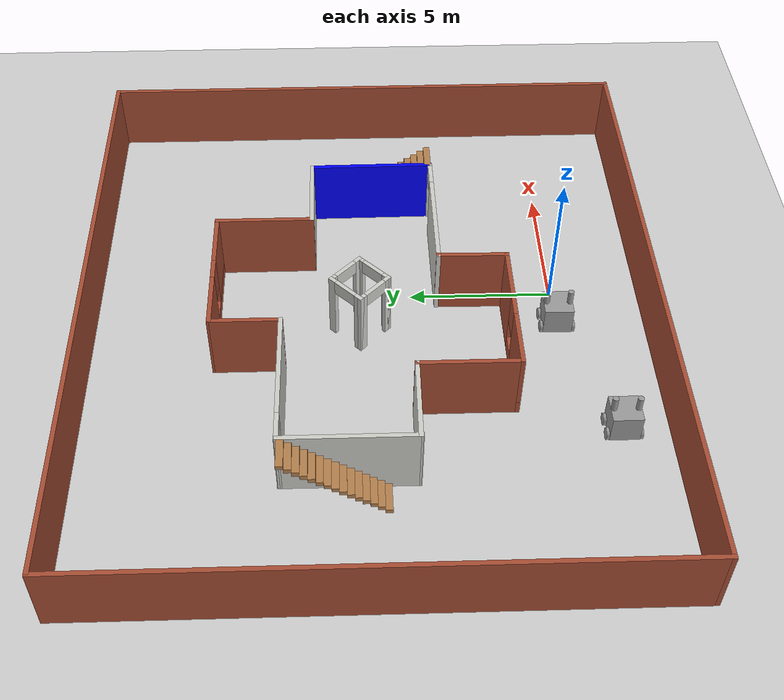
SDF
<sdf version="1.6">
 <world name="default">
  <plugin name="hello" filename="libhello.so"/>
  <light name="sun" type="directional">
   <pose>0 0 10 0 -0 0</pose>
   <diffuse>0.8 0.8 0.8 1</diffuse>
   <specular>0.2 0.2 0.2 1</specular>
   <attenuation>
    <range>1000</range>
    <constant>0.9</constant>
    <linear>0.01</linear>
    <quadratic>0.001</quadratic>
   </attenuation>
   <direction>-0.5 0.1 -0.9</direction>
  </light>
  <model name="ground_plane">
   <static>1</static>
   <link name="link">
    <collision name="collision">
     <geometry><plane><normal>0 0 1</normal><size>100 100</size></plane></geometry>
     <surface><friction><ode><mu>100</mu><mu2>50</mu2></ode></friction></surface>
    </collision>
    <visual name="visual">
     <cast_shadows>0</cast_shadows>
     <geometry><plane><normal>0 0 1</normal><size>100 100</size></plane></geometry>
     <material>
      <script><uri>file://media/materials/scripts/gazebo.material</uri><name>Gazebo/Grey</name></script>
     </material>
    </visual>
   </link>
  </model>
  <gravity>0 0 -9.8</gravity>
  <magnetic_field>6e-06 2.3e-05 -4.2e-05</magnetic_field>
  <atmosphere type="adiabatic"/>
  <physics name="default_physics" default="0" type="ode">
   <max_step_size>0.001</max_step_size>
   <real_time_factor>1</real_time_factor>
   <real_time_update_rate>1000</real_time_update_rate>
  </physics>
  <scene><ambient>0.4 0.4 0.4 1</ambient><background>0.7 0.7 0.7 1</background><shadows>1</shadows></scene>
  <spherical_coordinates>
   <surface_model>EARTH_WGS84</surface_model>
   <latitude_deg>0</latitude_deg>
   <longitude_deg>0</longitude_deg>
   <elevation>0</elevation>
   <heading_deg>0</heading_deg>
  </spherical_coordinates>
  <model name="GyandeepsRobot">
   <link name="link_0">
    <pose>-0.088094 0.807279 0.3325 0 -0 0</pose>
    <inertial>
     <mass>1</mass>
     <inertia>
      <ixx>0.166667</ixx>
      <ixy>0</ixy>
      <ixz>0</ixz>
      <iyy>0.166667</iyy>
      <iyz>0</iyz>
      <izz>0.166667</izz>
     </inertia>
    </inertial>
    <visual name="visual">
     <geometry><box><size>1 1 1</size></box></geometry>
     <material>
      <lighting>1</lighting>
      <script><uri>file://media/materials/scripts/gazebo.material</uri><name>Gazebo/Grey</name></script>
      <shader type="pixel"><normal_map>__default__</normal_map></shader>
      <ambient>0.3 0.3 0.3 1</ambient>
      <diffuse>0.7 0.7 0.7 1</diffuse>
      <specular>0.01 0.01 0.01 1</specular>
      <emissive>0 0 0 1</emissive>
     </material>
    </visual>
    <collision name="collision">
     <geometry><box><size>1 1 1</size></box></geometry>
     <surface>
      <friction>
       <ode><mu>1</mu><mu2>1</mu2><fdir1>0 0 0</fdir1><slip1>0</slip1><slip2>0</slip2></ode>
       <torsional>
        <coefficient>1</coefficient>
        <patch_radius>0</patch_radius>
        <surface_radius>0</surface_radius>
        <use_patch_radius>1</use_patch_radius>
        <ode><slip>0</slip></ode>
       </torsional>
      </friction>
      <bounce><restitution_coefficient>0</restitution_coefficient><threshold>1e+06</threshold></bounce>
      <contact>
       <collide_without_contact>0</collide_without_contact>
       <collide_without_contact_bitmask>1</collide_without_contact_bitmask>
       <collide_bitmask>1</collide_bitmask>
       <ode>
        <soft_cfm>0</soft_cfm>
        <soft_erp>0.2</soft_erp>
        <kp>1e+13</kp>
        <kd>1</kd>
        <max_vel>0.01</max_vel>
        <min_depth>0</min_depth>
       </ode>
       <bullet>
        <split_impulse>1</split_impulse>
        <split_impulse_penetration_threshold>-0.01</split_impulse_penetration_threshold>
        <soft_cfm>0</soft_cfm>
        <soft_erp>0.2</soft_erp>
        <kp>1e+13</kp>
        <kd>1</kd>
       </bullet>
      </contact>
     </surface>
    </collision>
   </link>
   <link name="link_1">
    <pose>-0.388094 0.257278 -0.0675 1.5708 -0 0</pose>
    <inertial>
     <mass>1</mass>
     <inertia><ixx>0.145833</ixx><ixy>0</ixy><ixz>0</ixz><iyy>0.145833</iyy><iyz>0</iyz><izz>0.125</izz></inertia>
    </inertial>
    <visual name="visual">
     <geometry><cylinder><radius>0.2</radius><length>0.1</length></cylinder></geometry>
     <material>
      <lighting>1</lighting>
      <script><uri>file://media/materials/scripts/gazebo.material</uri><name>Gazebo/Grey</name></script>
      <shader type="pixel"><normal_map>__default__</normal_map></shader>
      <ambient>0.3 0.3 0.3 1</ambient>
      <diffuse>0.7 0.7 0.7 1</diffuse>
      <specular>0.01 0.01 0.01 1</specular>
      <emissive>0 0 0 1</emissive>
     </material>
    </visual>
    <collision name="collision">
     <geometry><cylinder><radius>0.2</radius><length>0.1</length></cylinder></geometry>
     <surface>
      <friction>
       <ode><mu>1</mu><mu2>1</mu2><fdir1>0 0 0</fdir1><slip1>0</slip1><slip2>0</slip2></ode>
       <torsional>
        <coefficient>1</coefficient>
        <patch_radius>0</patch_radius>
        <surface_radius>0</surface_radius>
        <use_patch_radius>1</use_patch_radius>
        <ode><slip>0</slip></ode>
       </torsional>
      </friction>
      <bounce><restitution_coefficient>0</restitution_coefficient><threshold>1e+06</threshold></bounce>
      <contact>
       <collide_without_contact>0</collide_without_contact>
       <collide_without_contact_bitmask>1</collide_without_contact_bitmask>
       <collide_bitmask>1</collide_bitmask>
       <ode>
        <soft_cfm>0</soft_cfm>
        <soft_erp>0.2</soft_erp>
        <kp>1e+13</kp>
        <kd>1</kd>
        <max_vel>0.01</max_vel>
        <min_depth>0</min_depth>
       </ode>
       <bullet>
        <split_impulse>1</split_impulse>
        <split_impulse_penetration_threshold>-0.01</split_impulse_penetration_threshold>
        <soft_cfm>0</soft_cfm>
        <soft_erp>0.2</soft_erp>
        <kp>1e+13</kp>
        <kd>1</kd>
       </bullet>
      </contact>
     </surface>
    </collision>
   </link>
   <link name="link_1_clone">
    <pose>0.211906 0.257278 -0.0675 1.5708 -0 0</pose>
    <inertial>
     <mass>1</mass>
     <inertia><ixx>0.145833</ixx><ixy>0</ixy><ixz>0</ixz><iyy>0.145833</iyy><iyz>0</iyz><izz>0.125</izz></inertia>
    </inertial>
    <visual name="visual">
     <geometry><cylinder><radius>0.2</radius><length>0.1</length></cylinder></geometry>
     <material>
      <lighting>1</lighting>
      <script><uri>file://media/materials/scripts/gazebo.material</uri><name>Gazebo/Grey</name></script>
      <shader type="pixel"><normal_map>__default__</normal_map></shader>
      <ambient>0.3 0.3 0.3 1</ambient>
      <diffuse>0.7 0.7 0.7 1</diffuse>
      <specular>0.01 0.01 0.01 1</specular>
      <emissive>0 0 0 1</emissive>
     </material>
    </visual>
    <collision name="collision">
     <geometry><cylinder><radius>0.2</radius><length>0.1</length></cylinder></geometry>
     <surface>
      <friction>
       <ode><mu>1</mu><mu2>1</mu2><fdir1>0 0 0</fdir1><slip1>0</slip1><slip2>0</slip2></ode>
       <torsional>
        <coefficient>1</coefficient>
        <patch_radius>0</patch_radius>
        <surface_radius>0</surface_radius>
        <use_patch_radius>1</use_patch_radius>
        <ode><slip>0</slip></ode>
       </torsional>
      </friction>
      <bounce><restitution_coefficient>0</restitution_coefficient><threshold>1e+06</threshold></bounce>
      <contact>
       <collide_without_contact>0</collide_without_contact>
       <collide_without_contact_bitmask>1</collide_without_contact_bitmask>
       <collide_bitmask>1</collide_bitmask>
       <ode>
        <soft_cfm>0</soft_cfm>
        <soft_erp>0.2</soft_erp>
        <kp>1e+13</kp>
        <kd>1</kd>
        <max_vel>0.01</max_vel>
        <min_depth>0</min_depth>
       </ode>
       <bullet>
        <split_impulse>1</split_impulse>
        <split_impulse_penetration_threshold>-0.01</split_impulse_penetration_threshold>
        <soft_cfm>0</soft_cfm>
        <soft_erp>0.2</soft_erp>
        <kp>1e+13</kp>
        <kd>1</kd>
       </bullet>
      </contact>
     </surface>
    </collision>
   </link>
   <link name="link_1_clone_0">
    <pose>-0.388094 1.35728 -0.0675 1.5708 -0 0</pose>
    <inertial>
     <mass>1</mass>
     <inertia><ixx>0.145833</ixx><ixy>0</ixy><ixz>0</ixz><iyy>0.145833</iyy><iyz>0</iyz><izz>0.125</izz></inertia>
    </inertial>
    <visual name="visual">
     <geometry><cylinder><radius>0.2</radius><length>0.1</length></cylinder></geometry>
     <material>
      <lighting>1</lighting>
      <script><uri>file://media/materials/scripts/gazebo.material</uri><name>Gazebo/Grey</name></script>
      <shader type="pixel"><normal_map>__default__</normal_map></shader>
      <ambient>0.3 0.3 0.3 1</ambient>
      <diffuse>0.7 0.7 0.7 1</diffuse>
      <specular>0.01 0.01 0.01 1</specular>
      <emissive>0 0 0 1</emissive>
     </material>
    </visual>
    <collision name="collision">
     <geometry><cylinder><radius>0.2</radius><length>0.1</length></cylinder></geometry>
     <surface>
      <friction>
       <ode><mu>1</mu><mu2>1</mu2><fdir1>0 0 0</fdir1><slip1>0</slip1><slip2>0</slip2></ode>
       <torsional>
        <coefficient>1</coefficient>
        <patch_radius>0</patch_radius>
        <surface_radius>0</surface_radius>
        <use_patch_radius>1</use_patch_radius>
        <ode><slip>0</slip></ode>
       </torsional>
      </friction>
      <bounce><restitution_coefficient>0</restitution_coefficient><threshold>1e+06</threshold></bounce>
      <contact>
       <collide_without_contact>0</collide_without_contact>
       <collide_without_contact_bitmask>1</collide_without_contact_bitmask>
       <collide_bitmask>1</collide_bitmask>
       <ode>
        <soft_cfm>0</soft_cfm>
        <soft_erp>0.2</soft_erp>
        <kp>1e+13</kp>
        <kd>1</kd>
        <max_vel>0.01</max_vel>
        <min_depth>0</min_depth>
       </ode>
       <bullet>
        <split_impulse>1</split_impulse>
        <split_impulse_penetration_threshold>-0.01</split_impulse_penetration_threshold>
        <soft_cfm>0</soft_cfm>
        <soft_erp>0.2</soft_erp>
        <kp>1e+13</kp>
        <kd>1</kd>
       </bullet>
      </contact>
     </surface>
    </collision>
   </link>
   <link name="link_1_clone_1">
    <pose>0.211906 1.35728 -0.0675 1.5708 -0 0</pose>
    <inertial>
     <mass>1</mass>
     <inertia><ixx>0.145833</ixx><ixy>0</ixy><ixz>0</ixz><iyy>0.145833</iyy><iyz>0</iyz><izz>0.125</izz></inertia>
    </inertial>
    <visual name="visual">
     <geometry><cylinder><radius>0.2</radius><length>0.1</length></cylinder></geometry>
     <material>
      <lighting>1</lighting>
      <script><uri>file://media/materials/scripts/gazebo.material</uri><name>Gazebo/Grey</name></script>
      <shader type="pixel"><normal_map>__default__</normal_map></shader>
      <ambient>0.3 0.3 0.3 1</ambient>
      <diffuse>0.7 0.7 0.7 1</diffuse>
      <specular>0.01 0.01 0.01 1</specular>
      <emissive>0 0 0 1</emissive>
     </material>
    </visual>
    <collision name="collision">
     <geometry><cylinder><radius>0.2</radius><length>0.1</length></cylinder></geometry>
     <surface>
      <friction>
       <ode><mu>1</mu><mu2>1</mu2><fdir1>0 0 0</fdir1><slip1>0</slip1><slip2>0</slip2></ode>
       <torsional>
        <coefficient>1</coefficient>
        <patch_radius>0</patch_radius>
        <surface_radius>0</surface_radius>
        <use_patch_radius>1</use_patch_radius>
        <ode><slip>0</slip></ode>
       </torsional>
      </friction>
      <bounce><restitution_coefficient>0</restitution_coefficient><threshold>1e+06</threshold></bounce>
      <contact>
       <collide_without_contact>0</collide_without_contact>
       <collide_without_contact_bitmask>1</collide_without_contact_bitmask>
       <collide_bitmask>1</collide_bitmask>
       <ode>
        <soft_cfm>0</soft_cfm>
        <soft_erp>0.2</soft_erp>
        <kp>1e+13</kp>
        <kd>1</kd>
        <max_vel>0.01</max_vel>
        <min_depth>0</min_depth>
       </ode>
       <bullet>
        <split_impulse>1</split_impulse>
        <split_impulse_penetration_threshold>-0.01</split_impulse_penetration_threshold>
        <soft_cfm>0</soft_cfm>
        <soft_erp>0.2</soft_erp>
        <kp>1e+13</kp>
        <kd>1</kd>
       </bullet>
      </contact>
     </surface>
    </collision>
   </link>
   <link name="link_4">
    <pose>-0.108094 0.407279 1.0825 0 -0 0</pose>
    <inertial>
     <mass>1</mass>
     <inertia><ixx>0.145833</ixx><ixy>0</ixy><ixz>0</ixz><iyy>0.145833</iyy><iyz>0</iyz><izz>0.125</izz></inertia>
    </inertial>
    <visual name="visual">
     <geometry><cylinder><radius>0.1</radius><length>0.5</length></cylinder></geometry>
     <material>
      <lighting>1</lighting>
      <script><uri>file://media/materials/scripts/gazebo.material</uri><name>Gazebo/Grey</name></script>
      <shader type="pixel"><normal_map>__default__</normal_map></shader>
      <ambient>0.3 0.3 0.3 1</ambient>
      <diffuse>0.7 0.7 0.7 1</diffuse>
      <specular>0.01 0.01 0.01 1</specular>
      <emissive>0 0 0 1</emissive>
     </material>
    </visual>
    <collision name="collision">
     <geometry><cylinder><radius>0.1</radius><length>0.5</length></cylinder></geometry>
     <surface>
      <friction>
       <ode><mu>1</mu><mu2>1</mu2><fdir1>0 0 0</fdir1><slip1>0</slip1><slip2>0</slip2></ode>
       <torsional>
        <coefficient>1</coefficient>
        <patch_radius>0</patch_radius>
        <surface_radius>0</surface_radius>
        <use_patch_radius>1</use_patch_radius>
        <ode><slip>0</slip></ode>
       </torsional>
      </friction>
      <bounce><restitution_coefficient>0</restitution_coefficient><threshold>1e+06</threshold></bounce>
      <contact>
       <collide_without_contact>0</collide_without_contact>
       <collide_without_contact_bitmask>1</collide_without_contact_bitmask>
       <collide_bitmask>1</collide_bitmask>
       <ode>
        <soft_cfm>0</soft_cfm>
        <soft_erp>0.2</soft_erp>
        <kp>1e+13</kp>
        <kd>1</kd>
        <max_vel>0.01</max_vel>
        <min_depth>0</min_depth>
       </ode>
       <bullet>
        <split_impulse>1</split_impulse>
        <split_impulse_penetration_threshold>-0.01</split_impulse_penetration_threshold>
        <soft_cfm>0</soft_cfm>
        <soft_erp>0.2</soft_erp>
        <kp>1e+13</kp>
        <kd>1</kd>
       </bullet>
      </contact>
     </surface>
    </collision>
   </link>
   <link name="link_4_clone">
    <pose>-0.088094 1.20728 1.0825 0 -0 0</pose>
    <inertial>
     <mass>1</mass>
     <inertia><ixx>0.145833</ixx><ixy>0</ixy><ixz>0</ixz><iyy>0.145833</iyy><iyz>0</iyz><izz>0.125</izz></inertia>
    </inertial>
    <visual name="visual">
     <geometry><cylinder><radius>0.1</radius><length>0.5</length></cylinder></geometry>
     <material>
      <lighting>1</lighting>
      <script><uri>file://media/materials/scripts/gazebo.material</uri><name>Gazebo/Grey</name></script>
      <shader type="pixel"><normal_map>__default__</normal_map></shader>
      <ambient>0.3 0.3 0.3 1</ambient>
      <diffuse>0.7 0.7 0.7 1</diffuse>
      <specular>0.01 0.01 0.01 1</specular>
      <emissive>0 0 0 1</emissive>
     </material>
    </visual>
    <collision name="collision">
     <geometry><cylinder><radius>0.1</radius><length>0.5</length></cylinder></geometry>
     <surface>
      <friction>
       <ode><mu>1</mu><mu2>1</mu2><fdir1>0 0 0</fdir1><slip1>0</slip1><slip2>0</slip2></ode>
       <torsional>
        <coefficient>1</coefficient>
        <patch_radius>0</patch_radius>
        <surface_radius>0</surface_radius>
        <use_patch_radius>1</use_patch_radius>
        <ode><slip>0</slip></ode>
       </torsional>
      </friction>
      <bounce><restitution_coefficient>0</restitution_coefficient><threshold>1e+06</threshold></bounce>
      <contact>
       <collide_without_contact>0</collide_without_contact>
       <collide_without_contact_bitmask>1</collide_without_contact_bitmask>
       <collide_bitmask>1</collide_bitmask>
       <ode>
        <soft_cfm>0</soft_cfm>
        <soft_erp>0.2</soft_erp>
        <kp>1e+13</kp>
        <kd>1</kd>
        <max_vel>0.01</max_vel>
        <min_depth>0</min_depth>
       </ode>
       <bullet>
        <split_impulse>1</split_impulse>
        <split_impulse_penetration_threshold>-0.01</split_impulse_penetration_threshold>
        <soft_cfm>0</soft_cfm>
        <soft_erp>0.2</soft_erp>
        <kp>1e+13</kp>
        <kd>1</kd>
       </bullet>
      </contact>
     </surface>
    </collision>
   </link>
   <joint name="link_0_JOINT_0" type="revolute">
    <parent>link_0</parent>
    <child>link_1</child>
    <axis>
     <xyz>0 0 1</xyz>
     <use_parent_model_frame>0</use_parent_model_frame>
     <limit>
      <lower>-1.79769e+308</lower>
      <upper>1.79769e+308</upper>
      <effort>-1</effort>
      <velocity>-1</velocity>
     </limit>
     <dynamics>
      <spring_reference>0</spring_reference>
      <spring_stiffness>0</spring_stiffness>
      <damping>0</damping>
      <friction>0</friction>
     </dynamics>
    </axis>
    <physics>
     <ode><limit><cfm>0</cfm><erp>0.2</erp></limit><suspension><cfm>0</cfm><erp>0.2</erp></suspension></ode>
    </physics>
   </joint>
   <joint name="link_0_JOINT_1" type="revolute">
    <parent>link_0</parent>
    <child>link_1_clone</child>
    <axis>
     <xyz>0 0 1</xyz>
     <use_parent_model_frame>0</use_parent_model_frame>
     <limit>
      <lower>-1.79769e+308</lower>
      <upper>1.79769e+308</upper>
      <effort>-1</effort>
      <velocity>-1</velocity>
     </limit>
     <dynamics>
      <spring_reference>0</spring_reference>
      <spring_stiffness>0</spring_stiffness>
      <damping>0</damping>
      <friction>0</friction>
     </dynamics>
    </axis>
    <physics>
     <ode><limit><cfm>0</cfm><erp>0.2</erp></limit><suspension><cfm>0</cfm><erp>0.2</erp></suspension></ode>
    </physics>
   </joint>
   <joint name="link_0_JOINT_2" type="revolute">
    <parent>link_0</parent>
    <child>link_1_clone_0</child>
    <axis>
     <xyz>0 0 1</xyz>
     <use_parent_model_frame>0</use_parent_model_frame>
     <limit>
      <lower>-1.79769e+308</lower>
      <upper>1.79769e+308</upper>
      <effort>-1</effort>
      <velocity>-1</velocity>
     </limit>
     <dynamics>
      <spring_reference>0</spring_reference>
      <spring_stiffness>0</spring_stiffness>
      <damping>0</damping>
      <friction>0</friction>
     </dynamics>
    </axis>
    <physics>
     <ode><limit><cfm>0</cfm><erp>0.2</erp></limit><suspension><cfm>0</cfm><erp>0.2</erp></suspension></ode>
    </physics>
   </joint>
   <joint name="link_0_JOINT_3" type="revolute">
    <parent>link_0</parent>
    <child>link_1_clone_1</child>
    <axis>
     <xyz>0 0 1</xyz>
     <use_parent_model_frame>0</use_parent_model_frame>
     <limit>
      <lower>-1.79769e+308</lower>
      <upper>1.79769e+308</upper>
      <effort>-1</effort>
      <velocity>-1</velocity>
     </limit>
     <dynamics>
      <spring_reference>0</spring_reference>
      <spring_stiffness>0</spring_stiffness>
      <damping>0</damping>
     </dynamics>
    </axis>
    <physics>
     <ode><limit><cfm>0</cfm><erp>0.2</erp></limit><suspension><cfm>0</cfm><erp>0.2</erp></suspension></ode>
    </physics>
   </joint>
   <joint name="link_0_JOINT_4" type="prismatic">
    <parent>link_0</parent>
    <child>link_4</child>
    <axis>
     <xyz>0 0 1</xyz>
     <use_parent_model_frame>0</use_parent_model_frame>
     <limit>
      <lower>-1.79769e+308</lower>
      <upper>1.79769e+308</upper>
      <effort>-1</effort>
      <velocity>-1</velocity>
     </limit>
     <dynamics>
      <spring_reference>0</spring_reference>
      <spring_stiffness>0</spring_stiffness>
      <damping>0</damping>
     </dynamics>
    </axis>
    <physics>
     <ode><limit><cfm>0</cfm><erp>0.2</erp></limit><suspension><cfm>0</cfm><erp>0.2</erp></suspension></ode>
    </physics>
   </joint>
   <joint name="link_0_JOINT_5" type="prismatic">
    <parent>link_0</parent>
    <child>link_4_clone</child>
    <axis>
     <xyz>0 0 1</xyz>
     <use_parent_model_frame>0</use_parent_model_frame>
     <limit>
      <lower>-1.79769e+308</lower>
      <upper>1.79769e+308</upper>
      <effort>-1</effort>
      <velocity>-1</velocity>
     </limit>
     <dynamics>
      <spring_reference>0</spring_reference>
      <spring_stiffness>0</spring_stiffness>
      <damping>0</damping>
     </dynamics>
    </axis>
    <physics>
     <ode><limit><cfm>0</cfm><erp>0.2</erp></limit><suspension><cfm>0</cfm><erp>0.2</erp></suspension></ode>
    </physics>
   </joint>
   <static>0</static>
   <pose>-1.3526 -0.84178 0.267497 2e-06 0 -0.010479</pose>
  </model>
  <model name="Gyandeeps_World">
   <pose>-1.66136 6.46044 0 0 -0 0</pose>
   <link name="Stairs_1">
    <visual name="Stairs_1_Visual_0">
     <pose>6.58293 0.987313 0.083333 0 -0 0</pose>
     <geometry><box><size>1 0.233333 0.166667</size></box></geometry>
     <material>
      <script><uri>file://media/materials/scripts/gazebo.material</uri><name>Gazebo/Wood</name></script>
      <ambient>1 1 1 1</ambient>
     </material>
     <meta><layer>0</layer></meta>
    </visual>
    <collision name="Stairs_1_Collision_0">
     <geometry><box><size>1 0.233333 0.166667</size></box></geometry>
     <pose>6.58293 0.987313 0.083333 0 -0 0</pose>
    </collision>
    <visual name="Stairs_1_Visual_1">
     <pose>6.58293 0.75398 0.25 0 -0 0</pose>
     <geometry><box><size>1 0.233333 0.166667</size></box></geometry>
     <material>
      <script><uri>file://media/materials/scripts/gazebo.material</uri><name>Gazebo/Wood</name></script>
      <ambient>1 1 1 1</ambient>
     </material>
     <meta><layer>0</layer></meta>
    </visual>
    <collision name="Stairs_1_Collision_1">
     <geometry><box><size>1 0.233333 0.166667</size></box></geometry>
     <pose>6.58293 0.75398 0.25 0 -0 0</pose>
    </collision>
    <visual name="Stairs_1_Visual_2">
     <pose>6.58293 0.520647 0.416667 0 -0 0</pose>
     <geometry><box><size>1 0.233333 0.166667</size></box></geometry>
     <material>
      <script><uri>file://media/materials/scripts/gazebo.material</uri><name>Gazebo/Wood</name></script>
      <ambient>1 1 1 1</ambient>
     </material>
     <meta><layer>0</layer></meta>
    </visual>
    <collision name="Stairs_1_Collision_2">
     <geometry><box><size>1 0.233333 0.166667</size></box></geometry>
     <pose>6.58293 0.520647 0.416667 0 -0 0</pose>
    </collision>
    <visual name="Stairs_1_Visual_3">
     <pose>6.58293 0.287313 0.583333 0 -0 0</pose>
     <geometry><box><size>1 0.233333 0.166667</size></box></geometry>
     <material>
      <script><uri>file://media/materials/scripts/gazebo.material</uri><name>Gazebo/Wood</name></script>
      <ambient>1 1 1 1</ambient>
     </material>
     <meta><layer>0</layer></meta>
    </visual>
    <collision name="Stairs_1_Collision_3">
     <geometry><box><size>1 0.233333 0.166667</size></box></geometry>
     <pose>6.58293 0.287313 0.583333 0 -0 0</pose>
    </collision>
    <visual name="Stairs_1_Visual_4">
     <pose>6.58293 0.05398 0.75 0 -0 0</pose>
     <geometry><box><size>1 0.233333 0.166667</size></box></geometry>
     <material>
      <script><uri>file://media/materials/scripts/gazebo.material</uri><name>Gazebo/Wood</name></script>
      <ambient>1 1 1 1</ambient>
     </material>
     <meta><layer>0</layer></meta>
    </visual>
    <collision name="Stairs_1_Collision_4">
     <geometry><box><size>1 0.233333 0.166667</size></box></geometry>
     <pose>6.58293 0.05398 0.75 0 -0 0</pose>
    </collision>
    <visual name="Stairs_1_Visual_5">
     <pose>6.58293 -0.179353 0.916667 0 -0 0</pose>
     <geometry><box><size>1 0.233333 0.166667</size></box></geometry>
     <material>
      <script><uri>file://media/materials/scripts/gazebo.material</uri><name>Gazebo/Wood</name></script>
      <ambient>1 1 1 1</ambient>
     </material>
     <meta><layer>0</layer></meta>
    </visual>
    <collision name="Stairs_1_Collision_5">
     <geometry><box><size>1 0.233333 0.166667</size></box></geometry>
     <pose>6.58293 -0.179353 0.916667 0 -0 0</pose>
    </collision>
    <visual name="Stairs_1_Visual_6">
     <pose>6.58293 -0.412687 1.08333 0 -0 0</pose>
     <geometry><box><size>1 0.233333 0.166667</size></box></geometry>
     <material>
      <script><uri>file://media/materials/scripts/gazebo.material</uri><name>Gazebo/Wood</name></script>
      <ambient>1 1 1 1</ambient>
     </material>
     <meta><layer>0</layer></meta>
    </visual>
    <collision name="Stairs_1_Collision_6">
     <geometry><box><size>1 0.233333 0.166667</size></box></geometry>
     <pose>6.58293 -0.412687 1.08333 0 -0 0</pose>
    </collision>
    <visual name="Stairs_1_Visual_7">
     <pose>6.58293 -0.64602 1.25 0 -0 0</pose>
     <geometry><box><size>1 0.233333 0.166667</size></box></geometry>
     <material>
      <script><uri>file://media/materials/scripts/gazebo.material</uri><name>Gazebo/Wood</name></script>
      <ambient>1 1 1 1</ambient>
     </material>
     <meta><layer>0</layer></meta>
    </visual>
    <collision name="Stairs_1_Collision_7">
     <geometry><box><size>1 0.233333 0.166667</size></box></geometry>
     <pose>6.58293 -0.64602 1.25 0 -0 0</pose>
    </collision>
    <visual name="Stairs_1_Visual_8">
     <pose>6.58293 -0.879353 1.41667 0 -0 0</pose>
     <geometry><box><size>1 0.233333 0.166667</size></box></geometry>
     <material>
      <script><uri>file://media/materials/scripts/gazebo.material</uri><name>Gazebo/Wood</name></script>
      <ambient>1 1 1 1</ambient>
     </material>
     <meta><layer>0</layer></meta>
    </visual>
    <collision name="Stairs_1_Collision_8">
     <geometry><box><size>1 0.233333 0.166667</size></box></geometry>
     <pose>6.58293 -0.879353 1.41667 0 -0 0</pose>
    </collision>
    <visual name="Stairs_1_Visual_9">
     <pose>6.58293 -1.11269 1.58333 0 -0 0</pose>
     <geometry><box><size>1 0.233333 0.166667</size></box></geometry>
     <material>
      <script><uri>file://media/materials/scripts/gazebo.material</uri><name>Gazebo/Wood</name></script>
      <ambient>1 1 1 1</ambient>
     </material>
     <meta><layer>0</layer></meta>
    </visual>
    <collision name="Stairs_1_Collision_9">
     <geometry><box><size>1 0.233333 0.166667</size></box></geometry>
     <pose>6.58293 -1.11269 1.58333 0 -0 0</pose>
    </collision>
    <visual name="Stairs_1_Visual_10">
     <pose>6.58293 -1.34602 1.75 0 -0 0</pose>
     <geometry><box><size>1 0.233333 0.166667</size></box></geometry>
     <material>
      <script><uri>file://media/materials/scripts/gazebo.material</uri><name>Gazebo/Wood</name></script>
      <ambient>1 1 1 1</ambient>
     </material>
     <meta><layer>0</layer></meta>
    </visual>
    <collision name="Stairs_1_Collision_10">
     <geometry><box><size>1 0.233333 0.166667</size></box></geometry>
     <pose>6.58293 -1.34602 1.75 0 -0 0</pose>
    </collision>
    <visual name="Stairs_1_Visual_11">
     <pose>6.58293 -1.57935 1.91667 0 -0 0</pose>
     <geometry><box><size>1 0.233333 0.166667</size></box></geometry>
     <material>
      <script><uri>file://media/materials/scripts/gazebo.material</uri><name>Gazebo/Wood</name></script>
      <ambient>1 1 1 1</ambient>
     </material>
     <meta><layer>0</layer></meta>
    </visual>
    <collision name="Stairs_1_Collision_11">
     <geometry><box><size>1 0.233333 0.166667</size></box></geometry>
     <pose>6.58293 -1.57935 1.91667 0 -0 0</pose>
    </collision>
    <visual name="Stairs_1_Visual_12">
     <pose>6.58293 -1.81269 2.08333 0 -0 0</pose>
     <geometry><box><size>1 0.233333 0.166667</size></box></geometry>
     <material>
      <script><uri>file://media/materials/scripts/gazebo.material</uri><name>Gazebo/Wood</name></script>
      <ambient>1 1 1 1</ambient>
     </material>
     <meta><layer>0</layer></meta>
    </visual>
    <collision name="Stairs_1_Collision_12">
     <geometry><box><size>1 0.233333 0.166667</size></box></geometry>
     <pose>6.58293 -1.81269 2.08333 0 -0 0</pose>
    </collision>
    <visual name="Stairs_1_Visual_13">
     <pose>6.58293 -2.04602 2.25 0 -0 0</pose>
     <geometry><box><size>1 0.233333 0.166667</size></box></geometry>
     <material>
      <script><uri>file://media/materials/scripts/gazebo.material</uri><name>Gazebo/Wood</name></script>
      <ambient>1 1 1 1</ambient>
     </material>
     <meta><layer>0</layer></meta>
    </visual>
    <collision name="Stairs_1_Collision_13">
     <geometry><box><size>1 0.233333 0.166667</size></box></geometry>
     <pose>6.58293 -2.04602 2.25 0 -0 0</pose>
    </collision>
    <visual name="Stairs_1_Visual_14">
     <pose>6.58293 -2.27935 2.41667 0 -0 0</pose>
     <geometry><box><size>1 0.233333 0.166667</size></box></geometry>
     <material>
      <script><uri>file://media/materials/scripts/gazebo.material</uri><name>Gazebo/Wood</name></script>
      <ambient>1 1 1 1</ambient>
     </material>
     <meta><layer>0</layer></meta>
    </visual>
    <collision name="Stairs_1_Collision_14">
     <geometry><box><size>1 0.233333 0.166667</size></box></geometry>
     <pose>6.58293 -2.27935 2.41667 0 -0 0</pose>
    </collision>
   </link>
   <link name="Stairs_2">
    <visual name="Stairs_2_Visual_0">
     <pose>-7.05865 -0.36 0.083333 0 -0 -3.14159</pose>
     <geometry><box><size>1 0.233333 0.166667</size></box></geometry>
     <material>
      <script><uri>file://media/materials/scripts/gazebo.material</uri><name>Gazebo/Wood</name></script>
      <ambient>1 1 1 1</ambient>
     </material>
     <meta><layer>0</layer></meta>
    </visual>
    <collision name="Stairs_2_Collision_0">
     <geometry><box><size>1 0.233333 0.166667</size></box></geometry>
     <pose>-7.05865 -0.36 0.083333 0 -0 -3.14159</pose>
    </collision>
    <visual name="Stairs_2_Visual_1">
     <pose>-7.05865 -0.126666 0.25 0 -0 -3.14159</pose>
     <geometry><box><size>1 0.233333 0.166667</size></box></geometry>
     <material>
      <script><uri>file://media/materials/scripts/gazebo.material</uri><name>Gazebo/Wood</name></script>
      <ambient>1 1 1 1</ambient>
     </material>
     <meta><layer>0</layer></meta>
    </visual>
    <collision name="Stairs_2_Collision_1">
     <geometry><box><size>1 0.233333 0.166667</size></box></geometry>
     <pose>-7.05865 -0.126666 0.25 0 -0 -3.14159</pose>
    </collision>
    <visual name="Stairs_2_Visual_2">
     <pose>-7.05865 0.106667 0.416667 0 -0 -3.14159</pose>
     <geometry><box><size>1 0.233333 0.166667</size></box></geometry>
     <material>
      <script><uri>file://media/materials/scripts/gazebo.material</uri><name>Gazebo/Wood</name></script>
      <ambient>1 1 1 1</ambient>
     </material>
     <meta><layer>0</layer></meta>
    </visual>
    <collision name="Stairs_2_Collision_2">
     <geometry><box><size>1 0.233333 0.166667</size></box></geometry>
     <pose>-7.05865 0.106667 0.416667 0 -0 -3.14159</pose>
    </collision>
    <visual name="Stairs_2_Visual_3">
     <pose>-7.05865 0.34 0.583333 0 -0 -3.14159</pose>
     <geometry><box><size>1 0.233333 0.166667</size></box></geometry>
     <material>
      <script><uri>file://media/materials/scripts/gazebo.material</uri><name>Gazebo/Wood</name></script>
      <ambient>1 1 1 1</ambient>
     </material>
     <meta><layer>0</layer></meta>
    </visual>
    <collision name="Stairs_2_Collision_3">
     <geometry><box><size>1 0.233333 0.166667</size></box></geometry>
     <pose>-7.05865 0.34 0.583333 0 -0 -3.14159</pose>
    </collision>
    <visual name="Stairs_2_Visual_4">
     <pose>-7.05865 0.573334 0.75 0 -0 -3.14159</pose>
     <geometry><box><size>1 0.233333 0.166667</size></box></geometry>
     <material>
      <script><uri>file://media/materials/scripts/gazebo.material</uri><name>Gazebo/Wood</name></script>
      <ambient>1 1 1 1</ambient>
     </material>
     <meta><layer>0</layer></meta>
    </visual>
    <collision name="Stairs_2_Collision_4">
     <geometry><box><size>1 0.233333 0.166667</size></box></geometry>
     <pose>-7.05865 0.573334 0.75 0 -0 -3.14159</pose>
    </collision>
    <visual name="Stairs_2_Visual_5">
     <pose>-7.05865 0.806667 0.916667 0 -0 -3.14159</pose>
     <geometry><box><size>1 0.233333 0.166667</size></box></geometry>
     <material>
      <script><uri>file://media/materials/scripts/gazebo.material</uri><name>Gazebo/Wood</name></script>
      <ambient>1 1 1 1</ambient>
     </material>
     <meta><layer>0</layer></meta>
    </visual>
    <collision name="Stairs_2_Collision_5">
     <geometry><box><size>1 0.233333 0.166667</size></box></geometry>
     <pose>-7.05865 0.806667 0.916667 0 -0 -3.14159</pose>
    </collision>
    <visual name="Stairs_2_Visual_6">
     <pose>-7.05865 1.04 1.08333 0 -0 -3.14159</pose>
     <geometry><box><size>1 0.233333 0.166667</size></box></geometry>
     <material>
      <script><uri>file://media/materials/scripts/gazebo.material</uri><name>Gazebo/Wood</name></script>
      <ambient>1 1 1 1</ambient>
     </material>
     <meta><layer>0</layer></meta>
    </visual>
    <collision name="Stairs_2_Collision_6">
     <geometry><box><size>1 0.233333 0.166667</size></box></geometry>
     <pose>-7.05865 1.04 1.08333 0 -0 -3.14159</pose>
    </collision>
    <visual name="Stairs_2_Visual_7">
     <pose>-7.05865 1.27333 1.25 0 -0 -3.14159</pose>
     <geometry><box><size>1 0.233333 0.166667</size></box></geometry>
     <material>
      <script><uri>file://media/materials/scripts/gazebo.material</uri><name>Gazebo/Wood</name></script>
      <ambient>1 1 1 1</ambient>
     </material>
     <meta><layer>0</layer></meta>
    </visual>
    <collision name="Stairs_2_Collision_7">
     <geometry><box><size>1 0.233333 0.166667</size></box></geometry>
     <pose>-7.05865 1.27333 1.25 0 -0 -3.14159</pose>
    </collision>
    <visual name="Stairs_2_Visual_8">
     <pose>-7.05865 1.50667 1.41667 0 -0 -3.14159</pose>
     <geometry><box><size>1 0.233333 0.166667</size></box></geometry>
     <material>
      <script><uri>file://media/materials/scripts/gazebo.material</uri><name>Gazebo/Wood</name></script>
      <ambient>1 1 1 1</ambient>
     </material>
     <meta><layer>0</layer></meta>
    </visual>
    <collision name="Stairs_2_Collision_8">
     <geometry><box><size>1 0.233333 0.166667</size></box></geometry>
     <pose>-7.05865 1.50667 1.41667 0 -0 -3.14159</pose>
    </collision>
    <visual name="Stairs_2_Visual_9">
     <pose>-7.05865 1.74 1.58333 0 -0 -3.14159</pose>
     <geometry><box><size>1 0.233333 0.166667</size></box></geometry>
     <material>
      <script><uri>file://media/materials/scripts/gazebo.material</uri><name>Gazebo/Wood</name></script>
      <ambient>1 1 1 1</ambient>
     </material>
     <meta><layer>0</layer></meta>
    </visual>
    <collision name="Stairs_2_Collision_9">
     <geometry><box><size>1 0.233333 0.166667</size></box></geometry>
     <pose>-7.05865 1.74 1.58333 0 -0 -3.14159</pose>
    </collision>
    <visual name="Stairs_2_Visual_10">
     <pose>-7.05865 1.97333 1.75 0 -0 -3.14159</pose>
     <geometry><box><size>1 0.233333 0.166667</size></box></geometry>
     <material>
      <script><uri>file://media/materials/scripts/gazebo.material</uri><name>Gazebo/Wood</name></script>
      <ambient>1 1 1 1</ambient>
     </material>
     <meta><layer>0</layer></meta>
    </visual>
    <collision name="Stairs_2_Collision_10">
     <geometry><box><size>1 0.233333 0.166667</size></box></geometry>
     <pose>-7.05865 1.97333 1.75 0 -0 -3.14159</pose>
    </collision>
    <visual name="Stairs_2_Visual_11">
     <pose>-7.05865 2.20667 1.91667 0 -0 -3.14159</pose>
     <geometry><box><size>1 0.233333 0.166667</size></box></geometry>
     <material>
      <script><uri>file://media/materials/scripts/gazebo.material</uri><name>Gazebo/Wood</name></script>
      <ambient>1 1 1 1</ambient>
     </material>
     <meta><layer>0</layer></meta>
    </visual>
    <collision name="Stairs_2_Collision_11">
     <geometry><box><size>1 0.233333 0.166667</size></box></geometry>
     <pose>-7.05865 2.20667 1.91667 0 -0 -3.14159</pose>
    </collision>
    <visual name="Stairs_2_Visual_12">
     <pose>-7.05865 2.44 2.08333 0 -0 -3.14159</pose>
     <geometry><box><size>1 0.233333 0.166667</size></box></geometry>
     <material>
      <script><uri>file://media/materials/scripts/gazebo.material</uri><name>Gazebo/Wood</name></script>
      <ambient>1 1 1 1</ambient>
     </material>
     <meta><layer>0</layer></meta>
    </visual>
    <collision name="Stairs_2_Collision_12">
     <geometry><box><size>1 0.233333 0.166667</size></box></geometry>
     <pose>-7.05865 2.44 2.08333 0 -0 -3.14159</pose>
    </collision>
    <visual name="Stairs_2_Visual_13">
     <pose>-7.05865 2.67333 2.25 0 -0 -3.14159</pose>
     <geometry><box><size>1 0.233333 0.166667</size></box></geometry>
     <material>
      <script><uri>file://media/materials/scripts/gazebo.material</uri><name>Gazebo/Wood</name></script>
      <ambient>1 1 1 1</ambient>
     </material>
     <meta><layer>0</layer></meta>
    </visual>
    <collision name="Stairs_2_Collision_13">
     <geometry><box><size>1 0.233333 0.166667</size></box></geometry>
     <pose>-7.05865 2.67333 2.25 0 -0 -3.14159</pose>
    </collision>
    <visual name="Stairs_2_Visual_14">
     <pose>-7.05865 2.90667 2.41667 0 -0 -3.14159</pose>
     <geometry><box><size>1 0.233333 0.166667</size></box></geometry>
     <material>
      <script><uri>file://media/materials/scripts/gazebo.material</uri><name>Gazebo/Wood</name></script>
      <ambient>1 1 1 1</ambient>
     </material>
     <meta><layer>0</layer></meta>
    </visual>
    <collision name="Stairs_2_Collision_14">
     <geometry><box><size>1 0.233333 0.166667</size></box></geometry>
     <pose>-7.05865 2.90667 2.41667 0 -0 -3.14159</pose>
    </collision>
   </link>
   <link name="Wall_11">
    <collision name="Wall_11_Collision">
     <geometry><box><size>3 0.15 2.5</size></box></geometry>
     <pose>0 0 1.25 0 -0 0</pose>
    </collision>
    <visual name="Wall_11_Visual">
     <pose>0 0 1.25 0 -0 0</pose>
     <geometry><box><size>3 0.15 2.5</size></box></geometry>
     <material>
      <script><uri>file://media/materials/scripts/gazebo.material</uri><name>Gazebo/CeilingTiled</name></script>
      <ambient>0 0 1 1</ambient>
     </material>
     <meta><layer>0</layer></meta>
    </visual>
    <pose>-5.06858 -1.3399 0 0 -0 3.12748</pose>
   </link>
   <link name="Wall_14">
    <collision name="Wall_14_Collision">
     <geometry><box><size>4.5 0.15 2.5</size></box></geometry>
     <pose>0 0 1.25 0 -0 0</pose>
    </collision>
    <visual name="Wall_14_Visual">
     <pose>0 0 1.25 0 -0 0</pose>
     <geometry><box><size>4.5 0.15 2.5</size></box></geometry>
     <material>
      <script><uri>file://media/materials/scripts/gazebo.material</uri><name>Gazebo/CeilingTiled</name></script>
      <ambient>0 0 1 1</ambient>
     </material>
     <meta><layer>0</layer></meta>
    </visual>
    <pose>-6.49358 0.835104 0 0 -0 1.5708</pose>
   </link>
   <link name="Wall_16">
    <pose>-4.06858 3.0101 0 0 0 -0.008294</pose>
    <visual name="Wall_16_Visual_0">
     <pose>-2.4257 0 1.25 0 -0 0</pose>
     <geometry><box><size>0.148605 0.15 2.5</size></box></geometry>
     <material>
      <script><uri>file://media/materials/scripts/gazebo.material</uri><name>Gazebo/CeilingTiled</name></script>
      <ambient>0 0 1 1</ambient>
     </material>
     <meta><layer>0</layer></meta>
    </visual>
    <collision name="Wall_16_Collision_0">
     <geometry><box><size>0.148605 0.15 2.5</size></box></geometry>
     <pose>-2.4257 0 1.25 0 -0 0</pose>
    </collision>
    <visual name="Wall_16_Visual_1">
     <pose>0.524303 0 1.25 0 -0 0</pose>
     <geometry><box><size>3.9514 0.15 2.5</size></box></geometry>
     <material>
      <script><uri>file://media/materials/scripts/gazebo.material</uri><name>Gazebo/CeilingTiled</name></script>
      <ambient>0 0 1 1</ambient>
     </material>
     <meta><layer>0</layer></meta>
    </visual>
    <collision name="Wall_16_Collision_1">
     <geometry><box><size>3.9514 0.15 2.5</size></box></geometry>
     <pose>0.524303 0 1.25 0 -0 0</pose>
    </collision>
    <visual name="Wall_16_Visual_2">
     <pose>-1.90139 0 2.25 0 -0 0</pose>
     <geometry><box><size>0.9 0.15 0.5</size></box></geometry>
     <material>
      <script><uri>file://media/materials/scripts/gazebo.material</uri><name>Gazebo/CeilingTiled</name></script>
      <ambient>0 0 1 1</ambient>
     </material>
     <meta><layer>0</layer></meta>
    </visual>
    <collision name="Wall_16_Collision_2">
     <geometry><box><size>0.9 0.15 0.5</size></box></geometry>
     <pose>-1.90139 0 2.25 0 -0 0</pose>
    </collision>
   </link>
   <link name="Wall_26">
    <pose>0.783421 5.32999 0 0 -0 0</pose>
    <visual name="Wall_26_Visual_0">
     <pose>-1.44949 0 1.25 0 -0 0</pose>
     <geometry><box><size>2.10103 0.15 2.5</size></box></geometry>
     <material>
      <script><uri>file://media/materials/scripts/gazebo.material</uri><name>Gazebo/Bricks</name></script>
      <ambient>0.996078 0.47451 0.0196078 1</ambient>
     </material>
     <meta><layer>0</layer></meta>
    </visual>
    <collision name="Wall_26_Collision_0">
     <geometry><box><size>2.10103 0.15 2.5</size></box></geometry>
     <pose>-1.44949 0 1.25 0 -0 0</pose>
    </collision>
    <visual name="Wall_26_Visual_1">
     <pose>1.05051 0 0.25 0 -0 0</pose>
     <geometry><box><size>2.89897 0.15 0.5</size></box></geometry>
     <material>
      <script><uri>file://media/materials/scripts/gazebo.material</uri><name>Gazebo/Bricks</name></script>
      <ambient>0.996078 0.47451 0.0196078 1</ambient>
     </material>
     <meta><layer>0</layer></meta>
    </visual>
    <collision name="Wall_26_Collision_1">
     <geometry><box><size>2.89897 0.15 0.5</size></box></geometry>
     <pose>1.05051 0 0.25 0 -0 0</pose>
    </collision>
    <visual name="Wall_26_Visual_2">
     <pose>1.45051 0 1.5 0 -0 0</pose>
     <geometry><box><size>2.09897 0.15 2</size></box></geometry>
     <material>
      <script><uri>file://media/materials/scripts/gazebo.material</uri><name>Gazebo/Bricks</name></script>
      <ambient>0.996078 0.47451 0.0196078 1</ambient>
     </material>
     <meta><layer>0</layer></meta>
    </visual>
    <collision name="Wall_26_Collision_2">
     <geometry><box><size>2.09897 0.15 2</size></box></geometry>
     <pose>1.45051 0 1.5 0 -0 0</pose>
    </collision>
    <visual name="Wall_26_Visual_3">
     <pose>0.001028 0 1.9 0 -0 0</pose>
     <geometry><box><size>0.8 0.15 1.2</size></box></geometry>
     <material>
      <script><uri>file://media/materials/scripts/gazebo.material</uri><name>Gazebo/Bricks</name></script>
      <ambient>0.996078 0.47451 0.0196078 1</ambient>
     </material>
     <meta><layer>0</layer></meta>
    </visual>
    <collision name="Wall_26_Collision_3">
     <geometry><box><size>0.8 0.15 1.2</size></box></geometry>
     <pose>0.001028 0 1.9 0 -0 0</pose>
    </collision>
   </link>
   <link name="Wall_27">
    <collision name="Wall_27_Collision">
     <geometry><box><size>3.48 0.15 2.5</size></box></geometry>
     <pose>0 0 1.25 0 -0 0</pose>
    </collision>
    <visual name="Wall_27_Visual">
     <pose>0 0 1.25 0 -0 0</pose>
     <geometry><box><size>3.48 0.15 2.5</size></box></geometry>
     <material>
      <script><uri>file://media/materials/scripts/gazebo.material</uri><name>Gazebo/Bricks</name></script>
      <ambient>0.996078 0.47451 0.0196078 1</ambient>
     </material>
     <meta><layer>0</layer></meta>
    </visual>
    <pose>3.20842 3.65499 0 0 0 -1.5708</pose>
   </link>
   <link name="Wall_29">
    <collision name="Wall_29_Collision">
     <geometry><box><size>4.5 0.15 2.5</size></box></geometry>
     <pose>0 0 1.25 0 -0 0</pose>
    </collision>
    <visual name="Wall_29_Visual">
     <pose>0 0 1.25 0 -0 0</pose>
     <geometry><box><size>4.5 0.15 2.5</size></box></geometry>
     <material>
      <script><uri>file://media/materials/scripts/gazebo.material</uri><name>Gazebo/Grey</name></script>
      <ambient>0 0 1 1</ambient>
     </material>
     <meta><layer>0</layer></meta>
    </visual>
    <pose>6.07653 -0.18501 0 0 -0 1.58004</pose>
   </link>
   <link name="Wall_30">
    <collision name="Wall_30_Collision">
     <geometry><box><size>2.998 0.15 2.5</size></box></geometry>
     <pose>0 0 1.25 0 -0 0</pose>
    </collision>
    <visual name="Wall_30_Visual">
     <pose>0 0 1.25 0 -0 0</pose>
     <geometry><box><size>2.998 0.15 2.5</size></box></geometry>
     <material>
      <script><uri>file://media/materials/scripts/gazebo.material</uri><name>Gazebo/CeilingTiled</name></script>
      <ambient>0 0 1 1</ambient>
     </material>
     <meta><layer>0</layer></meta>
    </visual>
    <pose>4.63242 1.98999 0 0 -0 3.14159</pose>
   </link>
   <link name="Wall_32">
    <pose>-0.288264 0.836119 0 0 0 -2.35619</pose>
    <visual name="Wall_32_Visual_0">
     <pose>-0.606035 0 1.25 0 -0 0</pose>
     <geometry><box><size>0.28793 0.15 2.5</size></box></geometry>
     <material>
      <script><uri>file://media/materials/scripts/gazebo.material</uri><name>Gazebo/CeilingTiled</name></script>
      <ambient>0 0.333333 0.498039 1</ambient>
     </material>
     <meta><layer>0</layer></meta>
    </visual>
    <collision name="Wall_32_Collision_0">
     <geometry><box><size>0.28793 0.15 2.5</size></box></geometry>
     <pose>-0.606035 0 1.25 0 -0 0</pose>
    </collision>
    <visual name="Wall_32_Visual_1">
     <pose>0.593965 0 1.25 0 -0 0</pose>
     <geometry><box><size>0.31207 0.15 2.5</size></box></geometry>
     <material>
      <script><uri>file://media/materials/scripts/gazebo.material</uri><name>Gazebo/CeilingTiled</name></script>
      <ambient>0 0.333333 0.498039 1</ambient>
     </material>
     <meta><layer>0</layer></meta>
    </visual>
    <collision name="Wall_32_Collision_1">
     <geometry><box><size>0.31207 0.15 2.5</size></box></geometry>
     <pose>0.593965 0 1.25 0 -0 0</pose>
    </collision>
    <visual name="Wall_32_Visual_2">
     <pose>-0.01207 0 2.25 0 -0 0</pose>
     <geometry><box><size>0.9 0.15 0.5</size></box></geometry>
     <material>
      <script><uri>file://media/materials/scripts/gazebo.material</uri><name>Gazebo/CeilingTiled</name></script>
      <ambient>0 0.333333 0.498039 1</ambient>
     </material>
     <meta><layer>0</layer></meta>
    </visual>
    <collision name="Wall_32_Collision_2">
     <geometry><box><size>0.9 0.15 0.5</size></box></geometry>
     <pose>-0.01207 0 2.25 0 -0 0</pose>
    </collision>
   </link>
   <link name="Wall_33">
    <pose>-0.288264 -0.118475 0 0 0 -0.785398</pose>
    <visual name="Wall_33_Visual_0">
     <pose>-0.595093 0 1.25 0 -0 0</pose>
     <geometry><box><size>0.309813 0.15 2.5</size></box></geometry>
     <material>
      <script><uri>file://media/materials/scripts/gazebo.material</uri><name>Gazebo/CeilingTiled</name></script>
      <ambient>0 0.333333 0.498039 1</ambient>
     </material>
     <meta><layer>0</layer></meta>
    </visual>
    <collision name="Wall_33_Collision_0">
     <geometry><box><size>0.309813 0.15 2.5</size></box></geometry>
     <pose>-0.595093 0 1.25 0 -0 0</pose>
    </collision>
    <visual name="Wall_33_Visual_1">
     <pose>0.604907 0 1.25 0 -0 0</pose>
     <geometry><box><size>0.290187 0.15 2.5</size></box></geometry>
     <material>
      <script><uri>file://media/materials/scripts/gazebo.material</uri><name>Gazebo/CeilingTiled</name></script>
      <ambient>0 0.333333 0.498039 1</ambient>
     </material>
     <meta><layer>0</layer></meta>
    </visual>
    <collision name="Wall_33_Collision_1">
     <geometry><box><size>0.290187 0.15 2.5</size></box></geometry>
     <pose>0.604907 0 1.25 0 -0 0</pose>
    </collision>
    <visual name="Wall_33_Visual_2">
     <pose>0.009813 0 2.25 0 -0 0</pose>
     <geometry><box><size>0.9 0.15 0.5</size></box></geometry>
     <material>
      <script><uri>file://media/materials/scripts/gazebo.material</uri><name>Gazebo/CeilingTiled</name></script>
      <ambient>0 0.333333 0.498039 1</ambient>
     </material>
     <meta><layer>0</layer></meta>
    </visual>
    <collision name="Wall_33_Collision_2">
     <geometry><box><size>0.9 0.15 0.5</size></box></geometry>
     <pose>0.009813 0 2.25 0 -0 0</pose>
    </collision>
   </link>
   <link name="Wall_34">
    <pose>0.66633 -0.118475 0 0 -0 0.785398</pose>
    <visual name="Wall_34_Visual_0">
     <pose>-0.593965 0 1.25 0 -0 0</pose>
     <geometry><box><size>0.31207 0.15 2.5</size></box></geometry>
     <material>
      <script><uri>file://media/materials/scripts/gazebo.material</uri><name>Gazebo/CeilingTiled</name></script>
      <ambient>0 0.333333 0.498039 1</ambient>
     </material>
     <meta><layer>0</layer></meta>
    </visual>
    <collision name="Wall_34_Collision_0">
     <geometry><box><size>0.31207 0.15 2.5</size></box></geometry>
     <pose>-0.593965 0 1.25 0 -0 0</pose>
    </collision>
    <visual name="Wall_34_Visual_1">
     <pose>0.606035 0 1.25 0 -0 0</pose>
     <geometry><box><size>0.28793 0.15 2.5</size></box></geometry>
     <material>
      <script><uri>file://media/materials/scripts/gazebo.material</uri><name>Gazebo/CeilingTiled</name></script>
      <ambient>0 0.333333 0.498039 1</ambient>
     </material>
     <meta><layer>0</layer></meta>
    </visual>
    <collision name="Wall_34_Collision_1">
     <geometry><box><size>0.28793 0.15 2.5</size></box></geometry>
     <pose>0.606035 0 1.25 0 -0 0</pose>
    </collision>
    <visual name="Wall_34_Visual_2">
     <pose>0.01207 0 2.25 0 -0 0</pose>
     <geometry><box><size>0.9 0.15 0.5</size></box></geometry>
     <material>
      <script><uri>file://media/materials/scripts/gazebo.material</uri><name>Gazebo/CeilingTiled</name></script>
      <ambient>0 0.333333 0.498039 1</ambient>
     </material>
     <meta><layer>0</layer></meta>
    </visual>
    <collision name="Wall_34_Collision_2">
     <geometry><box><size>0.9 0.15 0.5</size></box></geometry>
     <pose>0.01207 0 2.25 0 -0 0</pose>
    </collision>
   </link>
   <link name="Wall_35">
    <pose>0.66633 0.836119 0 0 -0 2.35619</pose>
    <visual name="Wall_35_Visual_0">
     <pose>-0.592539 0 1.25 0 -0 0</pose>
     <geometry><box><size>0.314921 0.15 2.5</size></box></geometry>
     <material>
      <script><uri>file://media/materials/scripts/gazebo.material</uri><name>Gazebo/CeilingTiled</name></script>
      <ambient>0 0.333333 0.498039 1</ambient>
     </material>
     <meta><layer>0</layer></meta>
    </visual>
    <collision name="Wall_35_Collision_0">
     <geometry><box><size>0.314921 0.15 2.5</size></box></geometry>
     <pose>-0.592539 0 1.25 0 -0 0</pose>
    </collision>
    <visual name="Wall_35_Visual_1">
     <pose>0.607461 0 1.25 0 -0 0</pose>
     <geometry><box><size>0.285079 0.15 2.5</size></box></geometry>
     <material>
      <script><uri>file://media/materials/scripts/gazebo.material</uri><name>Gazebo/CeilingTiled</name></script>
      <ambient>0 0.333333 0.498039 1</ambient>
     </material>
     <meta><layer>0</layer></meta>
    </visual>
    <collision name="Wall_35_Collision_1">
     <geometry><box><size>0.285079 0.15 2.5</size></box></geometry>
     <pose>0.607461 0 1.25 0 -0 0</pose>
    </collision>
    <visual name="Wall_35_Visual_2">
     <pose>0.014921 0 2.25 0 -0 0</pose>
     <geometry><box><size>0.9 0.15 0.5</size></box></geometry>
     <material>
      <script><uri>file://media/materials/scripts/gazebo.material</uri><name>Gazebo/CeilingTiled</name></script>
      <ambient>0 0.333333 0.498039 1</ambient>
     </material>
     <meta><layer>0</layer></meta>
    </visual>
    <collision name="Wall_35_Collision_2">
     <geometry><box><size>0.9 0.15 0.5</size></box></geometry>
     <pose>0.014921 0 2.25 0 -0 0</pose>
    </collision>
   </link>
   <link name="Wall_37">
    <collision name="Wall_37_Collision">
     <geometry><box><size>2.49 0.15 2.5</size></box></geometry>
     <pose>0 0 1.25 0 -0 0</pose>
    </collision>
    <visual name="Wall_37_Visual">
     <pose>0 0 1.25 0 -0 0</pose>
     <geometry><box><size>2.49 0.15 2.5</size></box></geometry>
     <material>
      <script><uri>file://media/materials/scripts/gazebo.material</uri><name>Gazebo/Bricks</name></script>
      <ambient>0.996078 0.47451 0.0196078 1</ambient>
     </material>
     <meta><layer>0</layer></meta>
    </visual>
    <pose>-1.64258 4.15999 0 0 0 -1.57165</pose>
   </link>
   <link name="Wall_41">
    <collision name="Wall_41_Collision">
     <geometry><box><size>22 0.15 2.5</size></box></geometry>
     <pose>0 0 1.25 0 -0 0</pose>
    </collision>
    <visual name="Wall_41_Visual">
     <pose>0 0 1.25 0 -0 0</pose>
     <geometry><box><size>22 0.15 2.5</size></box></geometry>
     <material>
      <script><uri>file://media/materials/scripts/gazebo.material</uri><name>Gazebo/Bricks</name></script>
      <ambient>1 1 1 1</ambient>
     </material>
     <meta><layer>0</layer></meta>
    </visual>
    <pose>0.033421 9.67999 0 0 -0 0</pose>
   </link>
   <link name="Wall_46">
    <collision name="Wall_46_Collision">
     <geometry><box><size>19.5 0.15 2.5</size></box></geometry>
     <pose>0 0 1.25 0 -0 0</pose>
    </collision>
    <visual name="Wall_46_Visual">
     <pose>0 0 1.25 0 -0 0</pose>
     <geometry><box><size>19.5 0.15 2.5</size></box></geometry>
     <material>
      <script><uri>file://media/materials/scripts/gazebo.material</uri><name>Gazebo/Bricks</name></script>
      <ambient>1 1 1 1</ambient>
     </material>
     <meta><layer>0</layer></meta>
    </visual>
    <pose>-10.9584 -0.004957 0 0 -0 1.5708</pose>
   </link>
   <link name="Wall_48">
    <collision name="Wall_48_Collision">
     <geometry><box><size>19.5 0.15 2.5</size></box></geometry>
     <pose>0 0 1.25 0 -0 0</pose>
    </collision>
    <visual name="Wall_48_Visual">
     <pose>0 0 1.25 0 -0 0</pose>
     <geometry><box><size>19.5 0.15 2.5</size></box></geometry>
     <material>
      <script><uri>file://media/materials/scripts/gazebo.material</uri><name>Gazebo/Bricks</name></script>
      <ambient>1 1 1 1</ambient>
     </material>
     <meta><layer>0</layer></meta>
    </visual>
    <pose>10.9584 0.00499 0 0 0 -1.5708</pose>
   </link>
   <link name="Wall_5">
    <pose>3.65153 -2.36001 0 0 -0 3.14159</pose>
    <visual name="Wall_5_Visual_0">
     <pose>-2.42289 0 1.25 0 -0 0</pose>
     <geometry><box><size>0.15422 0.15 2.5</size></box></geometry>
     <material>
      <script><uri>file://media/materials/scripts/gazebo.material</uri><name>Gazebo/CeilingTiled</name></script>
      <ambient>0 0 1 1</ambient>
     </material>
     <meta><layer>0</layer></meta>
    </visual>
    <collision name="Wall_5_Collision_0">
     <geometry><box><size>0.15422 0.15 2.5</size></box></geometry>
     <pose>-2.42289 0 1.25 0 -0 0</pose>
    </collision>
    <visual name="Wall_5_Visual_1">
     <pose>0.52711 0 1.25 0 -0 0</pose>
     <geometry><box><size>3.94578 0.15 2.5</size></box></geometry>
     <material>
      <script><uri>file://media/materials/scripts/gazebo.material</uri><name>Gazebo/CeilingTiled</name></script>
      <ambient>0 0 1 1</ambient>
     </material>
     <meta><layer>0</layer></meta>
    </visual>
    <collision name="Wall_5_Collision_1">
     <geometry><box><size>3.94578 0.15 2.5</size></box></geometry>
     <pose>0.52711 0 1.25 0 -0 0</pose>
    </collision>
    <visual name="Wall_5_Visual_2">
     <pose>-1.89578 0 2.25 0 -0 0</pose>
     <geometry><box><size>0.9 0.15 0.5</size></box></geometry>
     <material>
      <script><uri>file://media/materials/scripts/gazebo.material</uri><name>Gazebo/CeilingTiled</name></script>
      <ambient>0 0 1 1</ambient>
     </material>
     <meta><layer>0</layer></meta>
    </visual>
    <collision name="Wall_5_Collision_2">
     <geometry><box><size>0.9 0.15 0.5</size></box></geometry>
     <pose>-1.89578 0 2.25 0 -0 0</pose>
    </collision>
   </link>
   <link name="Wall_50">
    <collision name="Wall_50_Collision">
     <geometry><box><size>22.0668 0.15 2.5</size></box></geometry>
     <pose>0 0 1.25 0 -0 0</pose>
    </collision>
    <visual name="Wall_50_Visual">
     <pose>0 0 1.25 0 -0 0</pose>
     <geometry><box><size>22.0668 0.15 2.5</size></box></geometry>
     <material>
      <script><uri>file://media/materials/scripts/gazebo.material</uri><name>Gazebo/Bricks</name></script>
      <ambient>1 1 1 1</ambient>
     </material>
     <meta><layer>0</layer></meta>
    </visual>
    <pose>0 -9.67498 0 0 -0 0.000454</pose>
   </link>
   <link name="Wall_7">
    <collision name="Wall_7_Collision">
     <geometry><box><size>2.5 0.15 2.5</size></box></geometry>
     <pose>0 0 1.25 0 -0 0</pose>
    </collision>
    <visual name="Wall_7_Visual">
     <pose>0 0 1.25 0 -0 0</pose>
     <geometry><box><size>2.5 0.15 2.5</size></box></geometry>
     <material>
      <script><uri>file://media/materials/scripts/gazebo.material</uri><name>Gazebo/Bricks</name></script>
      <ambient>0.996078 0.47451 0.0196078 1</ambient>
     </material>
     <meta><layer>0</layer></meta>
    </visual>
    <pose>1.22653 -3.53501 0 0 0 -1.58791</pose>
   </link>
   <link name="Wall_8">
    <pose>-1.21858 -4.71001 0 0 -0 3.14159</pose>
    <visual name="Wall_8_Visual_0">
     <pose>-1.45289 0 1.25 0 -0 0</pose>
     <geometry><box><size>2.09422 0.15 2.5</size></box></geometry>
     <material>
      <script><uri>file://media/materials/scripts/gazebo.material</uri><name>Gazebo/Bricks</name></script>
      <ambient>0.996078 0.47451 0.0196078 1</ambient>
     </material>
     <meta><layer>0</layer></meta>
    </visual>
    <collision name="Wall_8_Collision_0">
     <geometry><box><size>2.09422 0.15 2.5</size></box></geometry>
     <pose>-1.45289 0 1.25 0 -0 0</pose>
    </collision>
    <visual name="Wall_8_Visual_1">
     <pose>1.04711 0 0.25 0 -0 0</pose>
     <geometry><box><size>2.90578 0.15 0.5</size></box></geometry>
     <material>
      <script><uri>file://media/materials/scripts/gazebo.material</uri><name>Gazebo/Bricks</name></script>
      <ambient>0.996078 0.47451 0.0196078 1</ambient>
     </material>
     <meta><layer>0</layer></meta>
    </visual>
    <collision name="Wall_8_Collision_1">
     <geometry><box><size>2.90578 0.15 0.5</size></box></geometry>
     <pose>1.04711 0 0.25 0 -0 0</pose>
    </collision>
    <visual name="Wall_8_Visual_2">
     <pose>1.44711 0 1.5 0 -0 0</pose>
     <geometry><box><size>2.10578 0.15 2</size></box></geometry>
     <material>
      <script><uri>file://media/materials/scripts/gazebo.material</uri><name>Gazebo/Bricks</name></script>
      <ambient>0.996078 0.47451 0.0196078 1</ambient>
     </material>
     <meta><layer>0</layer></meta>
    </visual>
    <collision name="Wall_8_Collision_2">
     <geometry><box><size>2.10578 0.15 2</size></box></geometry>
     <pose>1.44711 0 1.5 0 -0 0</pose>
    </collision>
    <visual name="Wall_8_Visual_3">
     <pose>-0.00578 0 1.9 0 -0 0</pose>
     <geometry><box><size>0.8 0.15 1.2</size></box></geometry>
     <material>
      <script><uri>file://media/materials/scripts/gazebo.material</uri><name>Gazebo/Bricks</name></script>
      <ambient>0.996078 0.47451 0.0196078 1</ambient>
     </material>
     <meta><layer>0</layer></meta>
    </visual>
    <collision name="Wall_8_Collision_3">
     <geometry><box><size>0.8 0.15 1.2</size></box></geometry>
     <pose>-0.00578 0 1.9 0 -0 0</pose>
    </collision>
   </link>
   <link name="Wall_9">
    <collision name="Wall_9_Collision">
     <geometry><box><size>3.5 0.15 2.5</size></box></geometry>
     <pose>0 0 1.25 0 -0 0</pose>
    </collision>
    <visual name="Wall_9_Visual">
     <pose>0 0 1.25 0 -0 0</pose>
     <geometry><box><size>3.5 0.15 2.5</size></box></geometry>
     <material>
      <script><uri>file://media/materials/scripts/gazebo.material</uri><name>Gazebo/Bricks</name></script>
      <ambient>0.996078 0.47451 0.0196078 1</ambient>
     </material>
     <meta><layer>0</layer></meta>
    </visual>
    <pose>-3.64358 -3.03501 0 0 -0 1.5708</pose>
   </link>
   <static>1</static>
  </model>
  <model name="GyandeepsRobot_0">
   <link name="link_0">
    <pose>-0.088094 0.807279 0.3325 0 -0 0</pose>
    <inertial>
     <mass>1</mass>
     <inertia>
      <ixx>0.166667</ixx>
      <ixy>0</ixy>
      <ixz>0</ixz>
      <iyy>0.166667</iyy>
      <iyz>0</iyz>
      <izz>0.166667</izz>
     </inertia>
    </inertial>
    <visual name="visual">
     <geometry><box><size>1 1 1</size></box></geometry>
     <material>
      <lighting>1</lighting>
      <script><uri>file://media/materials/scripts/gazebo.material</uri><name>Gazebo/Grey</name></script>
      <shader type="pixel"><normal_map>__default__</normal_map></shader>
      <ambient>0.3 0.3 0.3 1</ambient>
      <diffuse>0.7 0.7 0.7 1</diffuse>
      <specular>0.01 0.01 0.01 1</specular>
      <emissive>0 0 0 1</emissive>
     </material>
    </visual>
    <collision name="collision">
     <geometry><box><size>1 1 1</size></box></geometry>
     <surface>
      <friction>
       <ode><mu>1</mu><mu2>1</mu2><fdir1>0 0 0</fdir1><slip1>0</slip1><slip2>0</slip2></ode>
       <torsional>
        <coefficient>1</coefficient>
        <patch_radius>0</patch_radius>
        <surface_radius>0</surface_radius>
        <use_patch_radius>1</use_patch_radius>
        <ode><slip>0</slip></ode>
       </torsional>
      </friction>
      <bounce><restitution_coefficient>0</restitution_coefficient><threshold>1e+06</threshold></bounce>
      <contact>
       <collide_without_contact>0</collide_without_contact>
       <collide_without_contact_bitmask>1</collide_without_contact_bitmask>
       <collide_bitmask>1</collide_bitmask>
       <ode>
        <soft_cfm>0</soft_cfm>
        <soft_erp>0.2</soft_erp>
        <kp>1e+13</kp>
        <kd>1</kd>
        <max_vel>0.01</max_vel>
        <min_depth>0</min_depth>
       </ode>
       <bullet>
        <split_impulse>1</split_impulse>
        <split_impulse_penetration_threshold>-0.01</split_impulse_penetration_threshold>
        <soft_cfm>0</soft_cfm>
        <soft_erp>0.2</soft_erp>
        <kp>1e+13</kp>
        <kd>1</kd>
       </bullet>
      </contact>
     </surface>
    </collision>
   </link>
   <link name="link_1">
    <pose>-0.388094 0.257278 -0.0675 1.5708 -0 0</pose>
    <inertial>
     <mass>1</mass>
     <inertia><ixx>0.145833</ixx><ixy>0</ixy><ixz>0</ixz><iyy>0.145833</iyy><iyz>0</iyz><izz>0.125</izz></inertia>
    </inertial>
    <visual name="visual">
     <geometry><cylinder><radius>0.2</radius><length>0.1</length></cylinder></geometry>
     <material>
      <lighting>1</lighting>
      <script><uri>file://media/materials/scripts/gazebo.material</uri><name>Gazebo/Grey</name></script>
      <shader type="pixel"><normal_map>__default__</normal_map></shader>
      <ambient>0.3 0.3 0.3 1</ambient>
      <diffuse>0.7 0.7 0.7 1</diffuse>
      <specular>0.01 0.01 0.01 1</specular>
      <emissive>0 0 0 1</emissive>
     </material>
    </visual>
    <collision name="collision">
     <geometry><cylinder><radius>0.2</radius><length>0.1</length></cylinder></geometry>
     <surface>
      <friction>
       <ode><mu>1</mu><mu2>1</mu2><fdir1>0 0 0</fdir1><slip1>0</slip1><slip2>0</slip2></ode>
       <torsional>
        <coefficient>1</coefficient>
        <patch_radius>0</patch_radius>
        <surface_radius>0</surface_radius>
        <use_patch_radius>1</use_patch_radius>
        <ode><slip>0</slip></ode>
       </torsional>
      </friction>
      <bounce><restitution_coefficient>0</restitution_coefficient><threshold>1e+06</threshold></bounce>
      <contact>
       <collide_without_contact>0</collide_without_contact>
       <collide_without_contact_bitmask>1</collide_without_contact_bitmask>
       <collide_bitmask>1</collide_bitmask>
       <ode>
        <soft_cfm>0</soft_cfm>
        <soft_erp>0.2</soft_erp>
        <kp>1e+13</kp>
        <kd>1</kd>
        <max_vel>0.01</max_vel>
        <min_depth>0</min_depth>
       </ode>
       <bullet>
        <split_impulse>1</split_impulse>
        <split_impulse_penetration_threshold>-0.01</split_impulse_penetration_threshold>
        <soft_cfm>0</soft_cfm>
        <soft_erp>0.2</soft_erp>
        <kp>1e+13</kp>
        <kd>1</kd>
       </bullet>
      </contact>
     </surface>
    </collision>
   </link>
   <link name="link_1_clone">
    <pose>0.211906 0.257278 -0.0675 1.5708 -0 0</pose>
    <inertial>
     <mass>1</mass>
     <inertia><ixx>0.145833</ixx><ixy>0</ixy><ixz>0</ixz><iyy>0.145833</iyy><iyz>0</iyz><izz>0.125</izz></inertia>
    </inertial>
    <visual name="visual">
     <geometry><cylinder><radius>0.2</radius><length>0.1</length></cylinder></geometry>
     <material>
      <lighting>1</lighting>
      <script><uri>file://media/materials/scripts/gazebo.material</uri><name>Gazebo/Grey</name></script>
      <shader type="pixel"><normal_map>__default__</normal_map></shader>
      <ambient>0.3 0.3 0.3 1</ambient>
      <diffuse>0.7 0.7 0.7 1</diffuse>
      <specular>0.01 0.01 0.01 1</specular>
      <emissive>0 0 0 1</emissive>
     </material>
    </visual>
    <collision name="collision">
     <geometry><cylinder><radius>0.2</radius><length>0.1</length></cylinder></geometry>
     <surface>
      <friction>
       <ode><mu>1</mu><mu2>1</mu2><fdir1>0 0 0</fdir1><slip1>0</slip1><slip2>0</slip2></ode>
       <torsional>
        <coefficient>1</coefficient>
        <patch_radius>0</patch_radius>
        <surface_radius>0</surface_radius>
        <use_patch_radius>1</use_patch_radius>
        <ode><slip>0</slip></ode>
       </torsional>
      </friction>
      <bounce><restitution_coefficient>0</restitution_coefficient><threshold>1e+06</threshold></bounce>
      <contact>
       <collide_without_contact>0</collide_without_contact>
       <collide_without_contact_bitmask>1</collide_without_contact_bitmask>
       <collide_bitmask>1</collide_bitmask>
       <ode>
        <soft_cfm>0</soft_cfm>
        <soft_erp>0.2</soft_erp>
        <kp>1e+13</kp>
        <kd>1</kd>
        <max_vel>0.01</max_vel>
        <min_depth>0</min_depth>
       </ode>
       <bullet>
        <split_impulse>1</split_impulse>
        <split_impulse_penetration_threshold>-0.01</split_impulse_penetration_threshold>
        <soft_cfm>0</soft_cfm>
        <soft_erp>0.2</soft_erp>
        <kp>1e+13</kp>
        <kd>1</kd>
       </bullet>
      </contact>
     </surface>
    </collision>
   </link>
   <link name="link_1_clone_0">
    <pose>-0.388094 1.35728 -0.0675 1.5708 -0 0</pose>
    <inertial>
     <mass>1</mass>
     <inertia><ixx>0.145833</ixx><ixy>0</ixy><ixz>0</ixz><iyy>0.145833</iyy><iyz>0</iyz><izz>0.125</izz></inertia>
    </inertial>
    <visual name="visual">
     <geometry><cylinder><radius>0.2</radius><length>0.1</length></cylinder></geometry>
     <material>
      <lighting>1</lighting>
      <script><uri>file://media/materials/scripts/gazebo.material</uri><name>Gazebo/Grey</name></script>
      <shader type="pixel"><normal_map>__default__</normal_map></shader>
      <ambient>0.3 0.3 0.3 1</ambient>
      <diffuse>0.7 0.7 0.7 1</diffuse>
      <specular>0.01 0.01 0.01 1</specular>
      <emissive>0 0 0 1</emissive>
     </material>
    </visual>
    <collision name="collision">
     <geometry><cylinder><radius>0.2</radius><length>0.1</length></cylinder></geometry>
     <surface>
      <friction>
       <ode><mu>1</mu><mu2>1</mu2><fdir1>0 0 0</fdir1><slip1>0</slip1><slip2>0</slip2></ode>
       <torsional>
        <coefficient>1</coefficient>
        <patch_radius>0</patch_radius>
        <surface_radius>0</surface_radius>
        <use_patch_radius>1</use_patch_radius>
        <ode><slip>0</slip></ode>
       </torsional>
      </friction>
      <bounce><restitution_coefficient>0</restitution_coefficient><threshold>1e+06</threshold></bounce>
      <contact>
       <collide_without_contact>0</collide_without_contact>
       <collide_without_contact_bitmask>1</collide_without_contact_bitmask>
       <collide_bitmask>1</collide_bitmask>
       <ode>
        <soft_cfm>0</soft_cfm>
        <soft_erp>0.2</soft_erp>
        <kp>1e+13</kp>
        <kd>1</kd>
        <max_vel>0.01</max_vel>
        <min_depth>0</min_depth>
       </ode>
       <bullet>
        <split_impulse>1</split_impulse>
        <split_impulse_penetration_threshold>-0.01</split_impulse_penetration_threshold>
        <soft_cfm>0</soft_cfm>
        <soft_erp>0.2</soft_erp>
        <kp>1e+13</kp>
        <kd>1</kd>
       </bullet>
      </contact>
     </surface>
    </collision>
   </link>
   <link name="link_1_clone_1">
    <pose>0.211906 1.35728 -0.0675 1.5708 -0 0</pose>
    <inertial>
     <mass>1</mass>
     <inertia><ixx>0.145833</ixx><ixy>0</ixy><ixz>0</ixz><iyy>0.145833</iyy><iyz>0</iyz><izz>0.125</izz></inertia>
    </inertial>
    <visual name="visual">
     <geometry><cylinder><radius>0.2</radius><length>0.1</length></cylinder></geometry>
     <material>
      <lighting>1</lighting>
      <script><uri>file://media/materials/scripts/gazebo.material</uri><name>Gazebo/Grey</name></script>
      <shader type="pixel"><normal_map>__default__</normal_map></shader>
      <ambient>0.3 0.3 0.3 1</ambient>
      <diffuse>0.7 0.7 0.7 1</diffuse>
      <specular>0.01 0.01 0.01 1</specular>
      <emissive>0 0 0 1</emissive>
     </material>
    </visual>
    <collision name="collision">
     <geometry><cylinder><radius>0.2</radius><length>0.1</length></cylinder></geometry>
     <surface>
      <friction>
       <ode><mu>1</mu><mu2>1</mu2><fdir1>0 0 0</fdir1><slip1>0</slip1><slip2>0</slip2></ode>
       <torsional>
        <coefficient>1</coefficient>
        <patch_radius>0</patch_radius>
        <surface_radius>0</surface_radius>
        <use_patch_radius>1</use_patch_radius>
        <ode><slip>0</slip></ode>
       </torsional>
      </friction>
      <bounce><restitution_coefficient>0</restitution_coefficient><threshold>1e+06</threshold></bounce>
      <contact>
       <collide_without_contact>0</collide_without_contact>
       <collide_without_contact_bitmask>1</collide_without_contact_bitmask>
       <collide_bitmask>1</collide_bitmask>
       <ode>
        <soft_cfm>0</soft_cfm>
        <soft_erp>0.2</soft_erp>
        <kp>1e+13</kp>
        <kd>1</kd>
        <max_vel>0.01</max_vel>
        <min_depth>0</min_depth>
       </ode>
       <bullet>
        <split_impulse>1</split_impulse>
        <split_impulse_penetration_threshold>-0.01</split_impulse_penetration_threshold>
        <soft_cfm>0</soft_cfm>
        <soft_erp>0.2</soft_erp>
        <kp>1e+13</kp>
        <kd>1</kd>
       </bullet>
      </contact>
     </surface>
    </collision>
   </link>
   <link name="link_4">
    <pose>-0.108094 0.407279 1.0825 0 -0 0</pose>
    <inertial>
     <mass>1</mass>
     <inertia><ixx>0.145833</ixx><ixy>0</ixy><ixz>0</ixz><iyy>0.145833</iyy><iyz>0</iyz><izz>0.125</izz></inertia>
    </inertial>
    <visual name="visual">
     <geometry><cylinder><radius>0.1</radius><length>0.5</length></cylinder></geometry>
     <material>
      <lighting>1</lighting>
      <script><uri>file://media/materials/scripts/gazebo.material</uri><name>Gazebo/Grey</name></script>
      <shader type="pixel"><normal_map>__default__</normal_map></shader>
      <ambient>0.3 0.3 0.3 1</ambient>
      <diffuse>0.7 0.7 0.7 1</diffuse>
      <specular>0.01 0.01 0.01 1</specular>
      <emissive>0 0 0 1</emissive>
     </material>
    </visual>
    <collision name="collision">
     <geometry><cylinder><radius>0.1</radius><length>0.5</length></cylinder></geometry>
     <surface>
      <friction>
       <ode><mu>1</mu><mu2>1</mu2><fdir1>0 0 0</fdir1><slip1>0</slip1><slip2>0</slip2></ode>
       <torsional>
        <coefficient>1</coefficient>
        <patch_radius>0</patch_radius>
        <surface_radius>0</surface_radius>
        <use_patch_radius>1</use_patch_radius>
        <ode><slip>0</slip></ode>
       </torsional>
      </friction>
      <bounce><restitution_coefficient>0</restitution_coefficient><threshold>1e+06</threshold></bounce>
      <contact>
       <collide_without_contact>0</collide_without_contact>
       <collide_without_contact_bitmask>1</collide_without_contact_bitmask>
       <collide_bitmask>1</collide_bitmask>
       <ode>
        <soft_cfm>0</soft_cfm>
        <soft_erp>0.2</soft_erp>
        <kp>1e+13</kp>
        <kd>1</kd>
        <max_vel>0.01</max_vel>
        <min_depth>0</min_depth>
       </ode>
       <bullet>
        <split_impulse>1</split_impulse>
        <split_impulse_penetration_threshold>-0.01</split_impulse_penetration_threshold>
        <soft_cfm>0</soft_cfm>
        <soft_erp>0.2</soft_erp>
        <kp>1e+13</kp>
        <kd>1</kd>
       </bullet>
      </contact>
     </surface>
    </collision>
   </link>
   <link name="link_4_clone">
    <pose>-0.088094 1.20728 1.0825 0 -0 0</pose>
    <inertial>
     <mass>1</mass>
     <inertia><ixx>0.145833</ixx><ixy>0</ixy><ixz>0</ixz><iyy>0.145833</iyy><iyz>0</iyz><izz>0.125</izz></inertia>
    </inertial>
    <visual name="visual">
     <geometry><cylinder><radius>0.1</radius><length>0.5</length></cylinder></geometry>
     <material>
      <lighting>1</lighting>
      <script><uri>file://media/materials/scripts/gazebo.material</uri><name>Gazebo/Grey</name></script>
      <shader type="pixel"><normal_map>__default__</normal_map></shader>
      <ambient>0.3 0.3 0.3 1</ambient>
      <diffuse>0.7 0.7 0.7 1</diffuse>
      <specular>0.01 0.01 0.01 1</specular>
      <emissive>0 0 0 1</emissive>
     </material>
    </visual>
    <collision name="collision">
     <geometry><cylinder><radius>0.1</radius><length>0.5</length></cylinder></geometry>
     <surface>
      <friction>
       <ode><mu>1</mu><mu2>1</mu2><fdir1>0 0 0</fdir1><slip1>0</slip1><slip2>0</slip2></ode>
       <torsional>
        <coefficient>1</coefficient>
        <patch_radius>0</patch_radius>
        <surface_radius>0</surface_radius>
        <use_patch_radius>1</use_patch_radius>
        <ode><slip>0</slip></ode>
       </torsional>
      </friction>
      <bounce><restitution_coefficient>0</restitution_coefficient><threshold>1e+06</threshold></bounce>
      <contact>
       <collide_without_contact>0</collide_without_contact>
       <collide_without_contact_bitmask>1</collide_without_contact_bitmask>
       <collide_bitmask>1</collide_bitmask>
       <ode>
        <soft_cfm>0</soft_cfm>
        <soft_erp>0.2</soft_erp>
        <kp>1e+13</kp>
        <kd>1</kd>
        <max_vel>0.01</max_vel>
        <min_depth>0</min_depth>
       </ode>
       <bullet>
        <split_impulse>1</split_impulse>
        <split_impulse_penetration_threshold>-0.01</split_impulse_penetration_threshold>
        <soft_cfm>0</soft_cfm>
        <soft_erp>0.2</soft_erp>
        <kp>1e+13</kp>
        <kd>1</kd>
       </bullet>
      </contact>
     </surface>
    </collision>
   </link>
   <joint name="link_0_JOINT_0" type="revolute">
    <parent>link_0</parent>
    <child>link_1</child>
    <axis>
     <xyz>0 0 1</xyz>
     <use_parent_model_frame>0</use_parent_model_frame>
     <limit>
      <lower>-1.79769e+308</lower>
      <upper>1.79769e+308</upper>
      <effort>-1</effort>
      <velocity>-1</velocity>
     </limit>
     <dynamics>
      <spring_reference>0</spring_reference>
      <spring_stiffness>0</spring_stiffness>
      <damping>0</damping>
      <friction>0</friction>
     </dynamics>
    </axis>
    <physics>
     <ode><limit><cfm>0</cfm><erp>0.2</erp></limit><suspension><cfm>0</cfm><erp>0.2</erp></suspension></ode>
    </physics>
   </joint>
   <joint name="link_0_JOINT_1" type="revolute">
    <parent>link_0</parent>
    <child>link_1_clone</child>
    <axis>
     <xyz>0 0 1</xyz>
     <use_parent_model_frame>0</use_parent_model_frame>
     <limit>
      <lower>-1.79769e+308</lower>
      <upper>1.79769e+308</upper>
      <effort>-1</effort>
      <velocity>-1</velocity>
     </limit>
     <dynamics>
      <spring_reference>0</spring_reference>
      <spring_stiffness>0</spring_stiffness>
      <damping>0</damping>
      <friction>0</friction>
     </dynamics>
    </axis>
    <physics>
     <ode><limit><cfm>0</cfm><erp>0.2</erp></limit><suspension><cfm>0</cfm><erp>0.2</erp></suspension></ode>
    </physics>
   </joint>
   <joint name="link_0_JOINT_2" type="revolute">
    <parent>link_0</parent>
    <child>link_1_clone_0</child>
    <axis>
     <xyz>0 0 1</xyz>
     <use_parent_model_frame>0</use_parent_model_frame>
     <limit>
      <lower>-1.79769e+308</lower>
      <upper>1.79769e+308</upper>
      <effort>-1</effort>
      <velocity>-1</velocity>
     </limit>
     <dynamics>
      <spring_reference>0</spring_reference>
      <spring_stiffness>0</spring_stiffness>
      <damping>0</damping>
      <friction>0</friction>
     </dynamics>
    </axis>
    <physics>
     <ode><limit><cfm>0</cfm><erp>0.2</erp></limit><suspension><cfm>0</cfm><erp>0.2</erp></suspension></ode>
    </physics>
   </joint>
   <joint name="link_0_JOINT_3" type="revolute">
    <parent>link_0</parent>
    <child>link_1_clone_1</child>
    <axis>
     <xyz>0 0 1</xyz>
     <use_parent_model_frame>0</use_parent_model_frame>
     <limit>
      <lower>-1.79769e+308</lower>
      <upper>1.79769e+308</upper>
      <effort>-1</effort>
      <velocity>-1</velocity>
     </limit>
     <dynamics>
      <spring_reference>0</spring_reference>
      <spring_stiffness>0</spring_stiffness>
      <damping>0</damping>
     </dynamics>
    </axis>
    <physics>
     <ode><limit><cfm>0</cfm><erp>0.2</erp></limit><suspension><cfm>0</cfm><erp>0.2</erp></suspension></ode>
    </physics>
   </joint>
   <joint name="link_0_JOINT_4" type="prismatic">
    <parent>link_0</parent>
    <child>link_4</child>
    <axis>
     <xyz>0 0 1</xyz>
     <use_parent_model_frame>0</use_parent_model_frame>
     <limit>
      <lower>-1.79769e+308</lower>
      <upper>1.79769e+308</upper>
      <effort>-1</effort>
      <velocity>-1</velocity>
     </limit>
     <dynamics>
      <spring_reference>0</spring_reference>
      <spring_stiffness>0</spring_stiffness>
      <damping>0</damping>
     </dynamics>
    </axis>
    <physics>
     <ode><limit><cfm>0</cfm><erp>0.2</erp></limit><suspension><cfm>0</cfm><erp>0.2</erp></suspension></ode>
    </physics>
   </joint>
   <joint name="link_0_JOINT_5" type="prismatic">
    <parent>link_0</parent>
    <child>link_4_clone</child>
    <axis>
     <xyz>0 0 1</xyz>
     <use_parent_model_frame>0</use_parent_model_frame>
     <limit>
      <lower>-1.79769e+308</lower>
      <upper>1.79769e+308</upper>
      <effort>-1</effort>
      <velocity>-1</velocity>
     </limit>
     <dynamics>
      <spring_reference>0</spring_reference>
      <spring_stiffness>0</spring_stiffness>
      <damping>0</damping>
     </dynamics>
    </axis>
    <physics>
     <ode><limit><cfm>0</cfm><erp>0.2</erp></limit><suspension><cfm>0</cfm><erp>0.2</erp></suspension></ode>
    </physics>
   </joint>
   <static>0</static>
   <pose>-6.1131 -2.36922 0.267501 -1e-06 -1e-06 0.008501</pose>
  </model>
  <model name="my_ball">
   <link name="link_0">
    <inertial>
     <mass>1</mass>
     <inertia><ixx>0.1</ixx><ixy>0</ixy><ixz>0</ixz><iyy>0.1</iyy><iyz>0</iyz><izz>0.1</izz></inertia>
    </inertial>
    <visual name="visual">
     <geometry><sphere><radius>0.1</radius></sphere></geometry>
     <material>
      <lighting>1</lighting>
      <script><uri>file://media/materials/scripts/gazebo.material</uri><name>Gazebo/Grey</name></script>
      <shader type="pixel"><normal_map>__default__</normal_map></shader>
      <ambient>1 1 1 1</ambient>
      <diffuse>1 1 1 1</diffuse>
      <specular>1 1 1 1</specular>
      <emissive>1 1 1 1</emissive>
     </material>
    </visual>
    <collision name="collision">
     <geometry><sphere><radius>0.1</radius></sphere></geometry>
     <surface>
      <friction>
       <ode><mu>1</mu><mu2>1</mu2><fdir1>0 0 0</fdir1><slip1>0</slip1><slip2>0</slip2></ode>
       <torsional>
        <coefficient>1</coefficient>
        <patch_radius>0</patch_radius>
        <surface_radius>0</surface_radius>
        <use_patch_radius>1</use_patch_radius>
        <ode><slip>0</slip></ode>
       </torsional>
      </friction>
      <bounce><restitution_coefficient>0</restitution_coefficient><threshold>1e+06</threshold></bounce>
      <contact>
       <collide_without_contact>0</collide_without_contact>
       <collide_without_contact_bitmask>1</collide_without_contact_bitmask>
       <collide_bitmask>1</collide_bitmask>
       <ode>
        <soft_cfm>0</soft_cfm>
        <soft_erp>0.2</soft_erp>
        <kp>1e+13</kp>
        <kd>1</kd>
        <max_vel>0.01</max_vel>
        <min_depth>0</min_depth>
       </ode>
       <bullet>
        <split_impulse>1</split_impulse>
        <split_impulse_penetration_threshold>-0.01</split_impulse_penetration_threshold>
        <soft_cfm>0</soft_cfm>
        <soft_erp>0.2</soft_erp>
        <kp>1e+13</kp>
        <kd>1</kd>
       </bullet>
      </contact>
     </surface>
    </collision>
   </link>
   <static>0</static>
   <pose>0.916736 3.08407 0.1 0 -0 0</pose>
  </model>
 </world>
</sdf>
